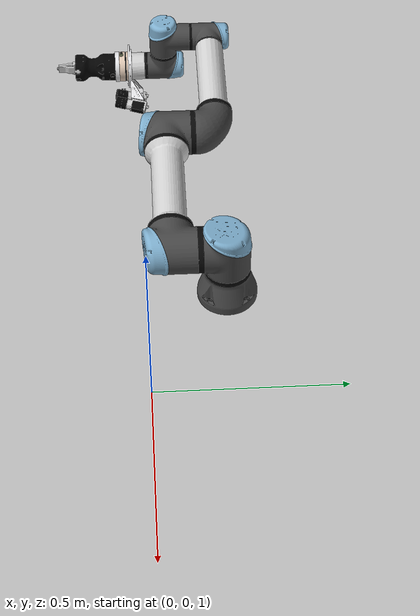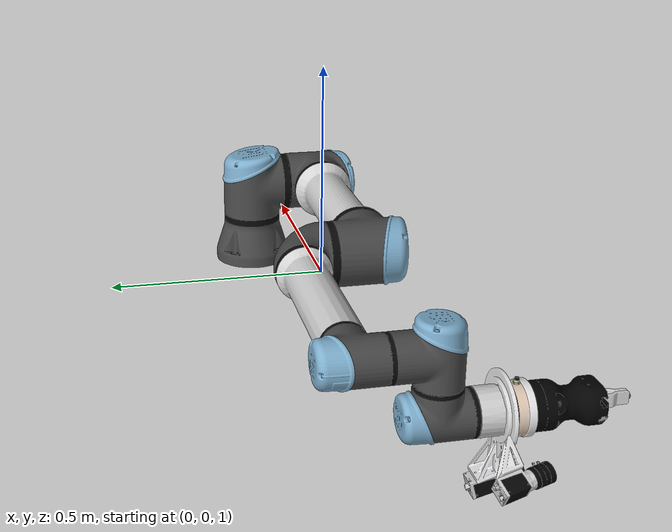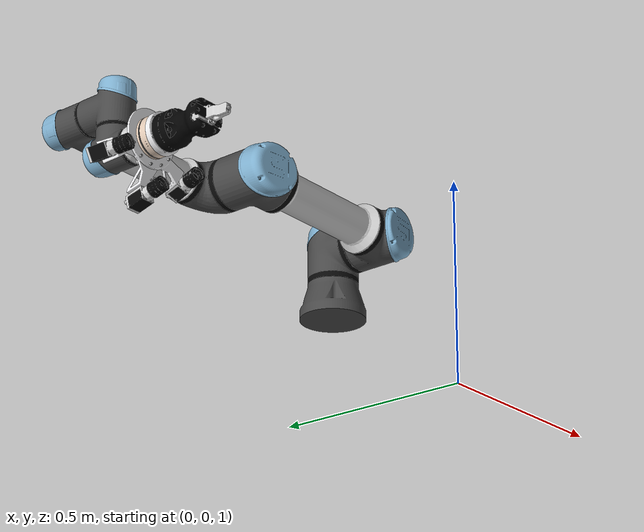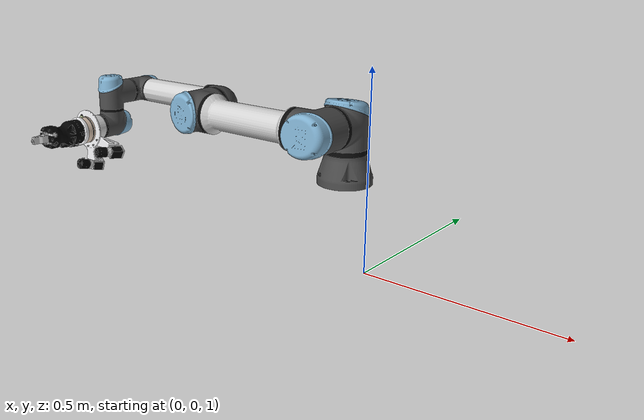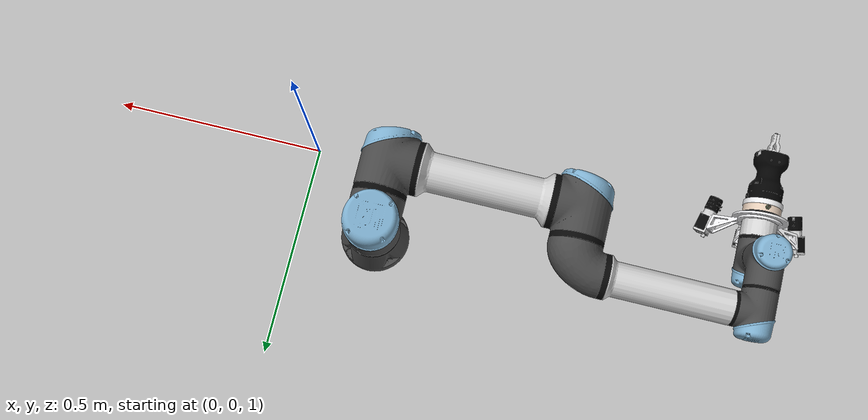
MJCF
<mujoco model="aic_world">
  <compiler angle="radian"/>

  <option gravity="0 0 -9.8" magnetic="5.5645e-06 2.28758e-05 -4.23884e-05"/>

  <visual>
    <global offwidth="1152" offheight="1024"/>
    <headlight ambient="0 0 0" diffuse="0 0 0" specular="0 0 0"/>
    <map znear="0.0025"/>
  </visual>

  <default>
    <default class="robot_unused"/>
  </default>

  <asset>
    <material name="material_bb4c831b689643226e5971fe331ef95e0c5c39f5d4107816252ab0347ed3238a_base_eSeries_UR5e_013-mesh" class="robot_unused" shininess="30" rgba="0.278431 0.278431 0.278431 1"/>
    <material name="material_bb4c831b689643226e5971fe331ef95e0c5c39f5d4107816252ab0347ed3238a_base_eSeries_UR5e_066-mesh" class="robot_unused" shininess="30" rgba="0.0313726 0.0313726 0.0313726 1"/>
    <material name="material_bb4c831b689643226e5971fe331ef95e0c5c39f5d4107816252ab0347ed3238a_shoulder_eSeries_UR5e_001-mesh" class="robot_unused" shininess="30" rgba="0.278431 0.278431 0.278431 1"/>
    <material name="material_bb4c831b689643226e5971fe331ef95e0c5c39f5d4107816252ab0347ed3238a_shoulder_eSeries_UR5e_067-mesh" class="robot_unused" shininess="30" rgba="0.0313726 0.0313726 0.0313726 1"/>
    <material name="material_bb4c831b689643226e5971fe331ef95e0c5c39f5d4107816252ab0347ed3238a_shoulder_eSeries_UR5e_068-mesh" class="robot_unused" shininess="30" rgba="0.490196 0.678431 0.8 1"/>
    <material name="material_bb4c831b689643226e5971fe331ef95e0c5c39f5d4107816252ab0347ed3238a_upperarm_merged_0" class="robot_unused" shininess="30" rgba="0.490196 0.678431 0.8 1"/>
    <material name="material_bb4c831b689643226e5971fe331ef95e0c5c39f5d4107816252ab0347ed3238a_upperarm_merged_1" class="robot_unused" shininess="30" rgba="0.278431 0.278431 0.278431 1"/>
    <material name="material_bb4c831b689643226e5971fe331ef95e0c5c39f5d4107816252ab0347ed3238a_upperarm_merged_2" class="robot_unused" shininess="30" rgba="0.0313726 0.0313726 0.0313726 1"/>
    <material name="material_bb4c831b689643226e5971fe331ef95e0c5c39f5d4107816252ab0347ed3238a_upperarm_eSeries_UR5e_073-mesh" class="robot_unused" shininess="30" rgba="0.819608 0.819608 0.819608 1"/>
    <material name="material_bb4c831b689643226e5971fe331ef95e0c5c39f5d4107816252ab0347ed3238a_forearm_merged_0" class="robot_unused" shininess="30" rgba="0.278431 0.278431 0.278431 1"/>
    <material name="material_bb4c831b689643226e5971fe331ef95e0c5c39f5d4107816252ab0347ed3238a_forearm_merged_1" class="robot_unused" shininess="30" rgba="0.0313726 0.0313726 0.0313726 1"/>
    <material name="material_bb4c831b689643226e5971fe331ef95e0c5c39f5d4107816252ab0347ed3238a_forearm_eSeries_UR5e_079-mesh" class="robot_unused" shininess="30" rgba="0.819608 0.819608 0.819608 1"/>
    <material name="material_bb4c831b689643226e5971fe331ef95e0c5c39f5d4107816252ab0347ed3238a_forearm_eSeries_UR5e_081-mesh" class="robot_unused" shininess="30" rgba="0.490196 0.678431 0.8 1"/>
    <material name="material_bb4c831b689643226e5971fe331ef95e0c5c39f5d4107816252ab0347ed3238a_wrist1_eSeries_UR5e_043-mesh" class="robot_unused" shininess="30" rgba="0.278431 0.278431 0.278431 1"/>
    <material name="material_bb4c831b689643226e5971fe331ef95e0c5c39f5d4107816252ab0347ed3238a_wrist1_eSeries_UR5e_083-mesh" class="robot_unused" shininess="30" rgba="0.490196 0.678431 0.8 1"/>
    <material name="material_bb4c831b689643226e5971fe331ef95e0c5c39f5d4107816252ab0347ed3238a_wrist1_eSeries_UR5e_084-mesh" class="robot_unused" shininess="30" rgba="0.0313726 0.0313726 0.0313726 1"/>
    <material name="material_bb4c831b689643226e5971fe331ef95e0c5c39f5d4107816252ab0347ed3238a_wrist2_eSeries_UR5e_049-mesh" class="robot_unused" shininess="30" rgba="0.278431 0.278431 0.278431 1"/>
    <material name="material_bb4c831b689643226e5971fe331ef95e0c5c39f5d4107816252ab0347ed3238a_wrist2_eSeries_UR5e_085-mesh" class="robot_unused" shininess="30" rgba="0.490196 0.678431 0.8 1"/>
    <material name="material_bb4c831b689643226e5971fe331ef95e0c5c39f5d4107816252ab0347ed3238a_wrist2_eSeries_UR5e_086-mesh" class="robot_unused" shininess="30" rgba="0.0313726 0.0313726 0.0313726 1"/>
    <material name="material_bb4c831b689643226e5971fe331ef95e0c5c39f5d4107816252ab0347ed3238a_wrist3_eSeries_UR5e_058-mesh" class="robot_unused" shininess="30" rgba="0.819608 0.819608 0.819608 1"/>
    <material name="material_77aecf6ee65958a58bba798a7e61b19213a681a9d1cfb48e37fb64f94dbd1ed2_cam_mount_visual_Cam_Mount.001" class="robot_unused" shininess="30" rgba="0.913725 0.913725 0.921569 1"/>
    <material name="material_77aecf6ee65958a58bba798a7e61b19213a681a9d1cfb48e37fb64f94dbd1ed2_cam_mount_visual_Cam_Mount.001_1" class="robot_unused" shininess="30" rgba="0.8 0.8 0.8 1"/>
    <material name="material_da0a7de639716d36573260e6b2cbbf5e041c6c33572c3d56607c19a7f3b4e1f0_basler_cam_visual_59871rev000.001" class="robot_unused" shininess="30" rgba="0.00784314 0.00784314 0.00784314 1"/>
    <material name="material_da0a7de639716d36573260e6b2cbbf5e041c6c33572c3d56607c19a7f3b4e1f0_basler_cam_visual_59871rev000.001_1" class="robot_unused" shininess="30" rgba="0.8 0.8 0.8 1"/>
    <material name="material_da0a7de639716d36573260e6b2cbbf5e041c6c33572c3d56607c19a7f3b4e1f0_basler_cam_visual_59871rev000.001_2" class="robot_unused" shininess="30" rgba="0.0196078 0.0196078 0.0196078 1"/>
    <material name="material_da0a7de639716d36573260e6b2cbbf5e041c6c33572c3d56607c19a7f3b4e1f0_basler_cam_visual_59871rev000.001_3" class="robot_unused" shininess="30" rgba="0.00392157 0.00392157 0.00392157 1"/>
    <material name="material_da0a7de639716d36573260e6b2cbbf5e041c6c33572c3d56607c19a7f3b4e1f0_basler_cam_visual_59871rev000.001_4" class="robot_unused" shininess="30" rgba="0.52549 0.52549 0.52549 1"/>
    <material name="material_ef10da9ad106c4dff912c5b813eab6adf887a181130890f0626184dba01c2bb2_axia_ft_sensor_visual_Axia80_M20.001" class="robot_unused" shininess="30" rgba="0.882353 0.792157 0.713726 1"/>
    <material name="material_ef10da9ad106c4dff912c5b813eab6adf887a181130890f0626184dba01c2bb2_axia_ft_sensor_visual_Axia80_M20.001_1" class="robot_unused" shininess="30" rgba="0.0196078 0.0196078 0.0196078 1"/>
    <material name="material_ef10da9ad106c4dff912c5b813eab6adf887a181130890f0626184dba01c2bb2_axia_ft_sensor_visual_Axia80_M20.001_2" class="robot_unused" shininess="30" rgba="0.8 0.564706 0.188235 1"/>
    <material name="material_ef10da9ad106c4dff912c5b813eab6adf887a181130890f0626184dba01c2bb2_axia_ft_sensor_visual_Axia80_M20.001_3" class="robot_unused" shininess="30" rgba="0.768627 0.811765 0.627451 1"/>
    <material name="material_ef10da9ad106c4dff912c5b813eab6adf887a181130890f0626184dba01c2bb2_axia_ft_sensor_visual_Axia80_M20.001_4" class="robot_unused" shininess="30" rgba="0.0117647 0.0117647 0.0117647 1"/>
    <material name="material_a356bb6a272d632104f139fc2b48a19577bee572dba59724b998cb71069c20f8_hande_base_visual_Cylinder.004" class="robot_unused" shininess="30" rgba="0.913725 0.913725 0.921569 1"/>
    <material name="material_a356bb6a272d632104f139fc2b48a19577bee572dba59724b998cb71069c20f8_hande_base_visual_Cylinder.004_1" class="robot_unused" shininess="30" rgba="0.00392157 0.00392157 0.00392157 1"/>
    <material name="material_a356bb6a272d632104f139fc2b48a19577bee572dba59724b998cb71069c20f8_hande_base_visual_Cylinder.004_2" class="robot_unused" shininess="30" rgba="0.784314 0.823529 0.847059 1"/>
    <material name="material_a356bb6a272d632104f139fc2b48a19577bee572dba59724b998cb71069c20f8_hande_base_visual_Cylinder.004_3" class="robot_unused" shininess="30" rgba="0.0117647 0.0117647 0.0117647 1"/>
    <material name="material_a356bb6a272d632104f139fc2b48a19577bee572dba59724b998cb71069c20f8_hande_base_visual_Cylinder.004_4" class="robot_unused" shininess="30" rgba="0.00784314 0.00784314 0.00784314 1"/>
    <material name="material_a356bb6a272d632104f139fc2b48a19577bee572dba59724b998cb71069c20f8_hande_base_visual_Cylinder.004_5" class="robot_unused" shininess="30" rgba="0.203922 0.203922 0.203922 1"/>
    <material name="material_a356bb6a272d632104f139fc2b48a19577bee572dba59724b998cb71069c20f8_hande_base_visual_Cylinder.004_6" class="robot_unused" shininess="30" rgba="0.5 0.5 0.5 1"/>
    <material name="material_a356bb6a272d632104f139fc2b48a19577bee572dba59724b998cb71069c20f8_hande_finger_visual_Finger.001" class="robot_unused" shininess="30" rgba="0.8 0.8 0.8 1"/>
    <mesh name="a0ab51268db2dd6ba30e2e14e1f8befeabfff6f0fbdfd420b564678df289a3c0_base.stl" class="robot_unused" content_type="model/stl" file="base-d994a04ff52ddcdf6d91bb6d4fcfff9b1425c18e.stl"/>
    <mesh name="bb4c831b689643226e5971fe331ef95e0c5c39f5d4107816252ab0347ed3238a_base_eSeries_UR5e_013-mesh" class="robot_unused" content_type="model/obj" file="bb4c831b689643226e5971fe331ef95e0c5c39f5d4107816252ab0347ed3238a_base_eSeries_UR5e_013-mesh-ae81e78d79cde8959e1b4051bcd48b43dd65d15f.obj" inertia="shell"/>
    <mesh name="bb4c831b689643226e5971fe331ef95e0c5c39f5d4107816252ab0347ed3238a_base_eSeries_UR5e_066-mesh" class="robot_unused" content_type="model/obj" file="bb4c831b689643226e5971fe331ef95e0c5c39f5d4107816252ab0347ed3238a_base_eSeries_UR5e_066-mesh-dd543f6667f50bd4643e49be303d92a0352f3d30.obj" inertia="shell"/>
    <mesh name="a0ab51268db2dd6ba30e2e14e1f8befeabfff6f0fbdfd420b564678df289a3c0_shoulder.stl" class="robot_unused" content_type="model/stl" file="shoulder-a83506202923a888b5b5d3c371edb9e13f236336.stl"/>
    <mesh name="bb4c831b689643226e5971fe331ef95e0c5c39f5d4107816252ab0347ed3238a_shoulder_eSeries_UR5e_001-mesh" class="robot_unused" content_type="model/obj" file="bb4c831b689643226e5971fe331ef95e0c5c39f5d4107816252ab0347ed3238a_shoulder_eSeries_UR5e_001-mesh-272c600201fcdab3fc8f4dad6fa4cd25579d6c3e.obj" inertia="shell"/>
    <mesh name="bb4c831b689643226e5971fe331ef95e0c5c39f5d4107816252ab0347ed3238a_shoulder_eSeries_UR5e_067-mesh" class="robot_unused" content_type="model/obj" file="bb4c831b689643226e5971fe331ef95e0c5c39f5d4107816252ab0347ed3238a_shoulder_eSeries_UR5e_067-mesh-ff08040e3ff3e66b2fcbba78dad276e67a66f2a9.obj" inertia="shell"/>
    <mesh name="bb4c831b689643226e5971fe331ef95e0c5c39f5d4107816252ab0347ed3238a_shoulder_eSeries_UR5e_068-mesh" class="robot_unused" content_type="model/obj" file="bb4c831b689643226e5971fe331ef95e0c5c39f5d4107816252ab0347ed3238a_shoulder_eSeries_UR5e_068-mesh-e6646b5927376d07178c45377b122d83ca5d8079.obj" inertia="shell"/>
    <mesh name="a0ab51268db2dd6ba30e2e14e1f8befeabfff6f0fbdfd420b564678df289a3c0_upperarm.stl" class="robot_unused" content_type="model/stl" file="upperarm-03c2bdced333d049d7ff8fbd721d7d8230d808bc.stl"/>
    <mesh name="bb4c831b689643226e5971fe331ef95e0c5c39f5d4107816252ab0347ed3238a_upperarm_merged_0" class="robot_unused" content_type="model/obj" file="bb4c831b689643226e5971fe331ef95e0c5c39f5d4107816252ab0347ed3238a_upperarm_merged_0-88fa3cf6b01946f867aa3ae8c3267e98b30b8869.obj" inertia="shell"/>
    <mesh name="bb4c831b689643226e5971fe331ef95e0c5c39f5d4107816252ab0347ed3238a_upperarm_merged_1" class="robot_unused" content_type="model/obj" file="bb4c831b689643226e5971fe331ef95e0c5c39f5d4107816252ab0347ed3238a_upperarm_merged_1-6caf0ab73dc274153cbd7f6f7ed6bb8d05f86b64.obj" inertia="shell"/>
    <mesh name="bb4c831b689643226e5971fe331ef95e0c5c39f5d4107816252ab0347ed3238a_upperarm_merged_2" class="robot_unused" content_type="model/obj" file="bb4c831b689643226e5971fe331ef95e0c5c39f5d4107816252ab0347ed3238a_upperarm_merged_2-ffa0d83ca1ca182a7f88f6b6370c57fb8458e1a1.obj" inertia="shell"/>
    <mesh name="bb4c831b689643226e5971fe331ef95e0c5c39f5d4107816252ab0347ed3238a_upperarm_eSeries_UR5e_073-mesh" class="robot_unused" content_type="model/obj" file="bb4c831b689643226e5971fe331ef95e0c5c39f5d4107816252ab0347ed3238a_upperarm_eSeries_UR5e_073-mesh-80ecc8c6aa2daa7af816d47c8b6c7336f8c8ab2e.obj" inertia="shell"/>
    <mesh name="a0ab51268db2dd6ba30e2e14e1f8befeabfff6f0fbdfd420b564678df289a3c0_forearm.stl" class="robot_unused" content_type="model/stl" file="forearm-95860729b3e4915567db264330b9ab276f0c8308.stl"/>
    <mesh name="bb4c831b689643226e5971fe331ef95e0c5c39f5d4107816252ab0347ed3238a_forearm_merged_0" class="robot_unused" content_type="model/obj" file="bb4c831b689643226e5971fe331ef95e0c5c39f5d4107816252ab0347ed3238a_forearm_merged_0-b1119653aa5b99527a8ffdc95deddded03606e49.obj" inertia="shell"/>
    <mesh name="bb4c831b689643226e5971fe331ef95e0c5c39f5d4107816252ab0347ed3238a_forearm_merged_1" class="robot_unused" content_type="model/obj" file="bb4c831b689643226e5971fe331ef95e0c5c39f5d4107816252ab0347ed3238a_forearm_merged_1-90d771496e3e60c8c49b0f907214218e12010f56.obj" inertia="shell"/>
    <mesh name="bb4c831b689643226e5971fe331ef95e0c5c39f5d4107816252ab0347ed3238a_forearm_eSeries_UR5e_079-mesh" class="robot_unused" content_type="model/obj" file="bb4c831b689643226e5971fe331ef95e0c5c39f5d4107816252ab0347ed3238a_forearm_eSeries_UR5e_079-mesh-3af239601fa1722841f61cefe776f3ac82925295.obj" inertia="shell"/>
    <mesh name="bb4c831b689643226e5971fe331ef95e0c5c39f5d4107816252ab0347ed3238a_forearm_eSeries_UR5e_081-mesh" class="robot_unused" content_type="model/obj" file="bb4c831b689643226e5971fe331ef95e0c5c39f5d4107816252ab0347ed3238a_forearm_eSeries_UR5e_081-mesh-295cc91f1da8d729521b96ae635c9f65e0f9235d.obj" inertia="shell"/>
    <mesh name="a0ab51268db2dd6ba30e2e14e1f8befeabfff6f0fbdfd420b564678df289a3c0_wrist1.stl" class="robot_unused" content_type="model/stl" file="wrist1-d0aff1dbf858639fbad7a22318ecfa5fba436f30.stl"/>
    <mesh name="bb4c831b689643226e5971fe331ef95e0c5c39f5d4107816252ab0347ed3238a_wrist1_eSeries_UR5e_043-mesh" class="robot_unused" content_type="model/obj" file="bb4c831b689643226e5971fe331ef95e0c5c39f5d4107816252ab0347ed3238a_wrist1_eSeries_UR5e_043-mesh-62b7c0392b368ddedc2465d9c00c00e610d20f5a.obj" inertia="shell"/>
    <mesh name="bb4c831b689643226e5971fe331ef95e0c5c39f5d4107816252ab0347ed3238a_wrist1_eSeries_UR5e_083-mesh" class="robot_unused" content_type="model/obj" file="bb4c831b689643226e5971fe331ef95e0c5c39f5d4107816252ab0347ed3238a_wrist1_eSeries_UR5e_083-mesh-cabbadefb6102d1556a4ee64c8bd36cad8056884.obj" inertia="shell"/>
    <mesh name="bb4c831b689643226e5971fe331ef95e0c5c39f5d4107816252ab0347ed3238a_wrist1_eSeries_UR5e_084-mesh" class="robot_unused" content_type="model/obj" file="bb4c831b689643226e5971fe331ef95e0c5c39f5d4107816252ab0347ed3238a_wrist1_eSeries_UR5e_084-mesh-ac1b41f582ea0ee06c11c0892f88e3251a6546be.obj" inertia="shell"/>
    <mesh name="a0ab51268db2dd6ba30e2e14e1f8befeabfff6f0fbdfd420b564678df289a3c0_wrist2.stl" class="robot_unused" content_type="model/stl" file="wrist2-777eba24b0996c38308995e2e7740d22a77ee8a8.stl"/>
    <mesh name="bb4c831b689643226e5971fe331ef95e0c5c39f5d4107816252ab0347ed3238a_wrist2_eSeries_UR5e_049-mesh" class="robot_unused" content_type="model/obj" file="bb4c831b689643226e5971fe331ef95e0c5c39f5d4107816252ab0347ed3238a_wrist2_eSeries_UR5e_049-mesh-1e943fb734424cb597a1a044d2099d5fdfbb4313.obj" inertia="shell"/>
    <mesh name="bb4c831b689643226e5971fe331ef95e0c5c39f5d4107816252ab0347ed3238a_wrist2_eSeries_UR5e_085-mesh" class="robot_unused" content_type="model/obj" file="bb4c831b689643226e5971fe331ef95e0c5c39f5d4107816252ab0347ed3238a_wrist2_eSeries_UR5e_085-mesh-60da050b95a6d5e25db5fe59ffab86db07961b4c.obj" inertia="shell"/>
    <mesh name="bb4c831b689643226e5971fe331ef95e0c5c39f5d4107816252ab0347ed3238a_wrist2_eSeries_UR5e_086-mesh" class="robot_unused" content_type="model/obj" file="bb4c831b689643226e5971fe331ef95e0c5c39f5d4107816252ab0347ed3238a_wrist2_eSeries_UR5e_086-mesh-a15e99ce0f74c0a8f995e5172279d0dfcac6845e.obj" inertia="shell"/>
    <mesh name="a0ab51268db2dd6ba30e2e14e1f8befeabfff6f0fbdfd420b564678df289a3c0_wrist3.stl" class="robot_unused" content_type="model/stl" file="wrist3-f7f56f92b9aad1eab55349b28bbe751f72de21da.stl"/>
    <mesh name="bb4c831b689643226e5971fe331ef95e0c5c39f5d4107816252ab0347ed3238a_wrist3_eSeries_UR5e_058-mesh" class="robot_unused" content_type="model/obj" file="bb4c831b689643226e5971fe331ef95e0c5c39f5d4107816252ab0347ed3238a_wrist3_eSeries_UR5e_058-mesh-67fef77ed5577e1d953e2e77da568e9a7d2cb750.obj" inertia="shell"/>
    <mesh name="77aecf6ee65958a58bba798a7e61b19213a681a9d1cfb48e37fb64f94dbd1ed2_cam_mount_visual_Cam_Mount.001" class="robot_unused" content_type="model/obj" file="77aecf6ee65958a58bba798a7e61b19213a681a9d1cfb48e37fb64f94dbd1ed2_cam_mount_visual_Cam_Mount.001-723ff43f362d0710a4bac575e9d2b9597ae995d6.obj" inertia="shell"/>
    <mesh name="77aecf6ee65958a58bba798a7e61b19213a681a9d1cfb48e37fb64f94dbd1ed2_cam_mount_visual_Cam_Mount.001_1" class="robot_unused" content_type="model/obj" file="77aecf6ee65958a58bba798a7e61b19213a681a9d1cfb48e37fb64f94dbd1ed2_cam_mount_visual_Cam_Mount.001_1-0c31e96946f6e4a992e40f16ffd143303f2fc693.obj" inertia="shell"/>
    <mesh name="da0a7de639716d36573260e6b2cbbf5e041c6c33572c3d56607c19a7f3b4e1f0_basler_cam_visual_59871rev000.001" class="robot_unused" content_type="model/obj" file="da0a7de639716d36573260e6b2cbbf5e041c6c33572c3d56607c19a7f3b4e1f0_basler_cam_visual_59871rev000.001-ea790e2c931ae136790eb9db5c9297b0a632fd93.obj" inertia="shell"/>
    <mesh name="da0a7de639716d36573260e6b2cbbf5e041c6c33572c3d56607c19a7f3b4e1f0_basler_cam_visual_59871rev000.001_1" class="robot_unused" content_type="model/obj" file="da0a7de639716d36573260e6b2cbbf5e041c6c33572c3d56607c19a7f3b4e1f0_basler_cam_visual_59871rev000.001_1-28ccf15525b0de2a7b9afa152d290efc33be18a4.obj" inertia="shell"/>
    <mesh name="da0a7de639716d36573260e6b2cbbf5e041c6c33572c3d56607c19a7f3b4e1f0_basler_cam_visual_59871rev000.001_2" class="robot_unused" content_type="model/obj" file="da0a7de639716d36573260e6b2cbbf5e041c6c33572c3d56607c19a7f3b4e1f0_basler_cam_visual_59871rev000.001_2-36c96f981e71c1cf6b31da79577e86d871a3ec2d.obj" inertia="shell"/>
    <mesh name="da0a7de639716d36573260e6b2cbbf5e041c6c33572c3d56607c19a7f3b4e1f0_basler_cam_visual_59871rev000.001_3" class="robot_unused" content_type="model/obj" file="da0a7de639716d36573260e6b2cbbf5e041c6c33572c3d56607c19a7f3b4e1f0_basler_cam_visual_59871rev000.001_3-11d42f5e41dcfed76206985524331834024f1c81.obj" inertia="shell"/>
    <mesh name="da0a7de639716d36573260e6b2cbbf5e041c6c33572c3d56607c19a7f3b4e1f0_basler_cam_visual_59871rev000.001_4" class="robot_unused" content_type="model/obj" file="da0a7de639716d36573260e6b2cbbf5e041c6c33572c3d56607c19a7f3b4e1f0_basler_cam_visual_59871rev000.001_4-5588717adcbdf83f1ff65b65be3ac368dbe69164.obj" inertia="shell"/>
    <mesh name="ef10da9ad106c4dff912c5b813eab6adf887a181130890f0626184dba01c2bb2_axia_ft_sensor_visual_Axia80_M20.001" class="robot_unused" content_type="model/obj" file="ef10da9ad106c4dff912c5b813eab6adf887a181130890f0626184dba01c2bb2_axia_ft_sensor_visual_Axia80_M20.001-e71568379caa7fc7691a233f5ef4487cf57b0b6a.obj" inertia="shell"/>
    <mesh name="ef10da9ad106c4dff912c5b813eab6adf887a181130890f0626184dba01c2bb2_axia_ft_sensor_visual_Axia80_M20.001_1" class="robot_unused" content_type="model/obj" file="ef10da9ad106c4dff912c5b813eab6adf887a181130890f0626184dba01c2bb2_axia_ft_sensor_visual_Axia80_M20.001_1-47b7cd0ada962512b0e7fc9aacb9d4a493a53870.obj" inertia="shell"/>
    <mesh name="ef10da9ad106c4dff912c5b813eab6adf887a181130890f0626184dba01c2bb2_axia_ft_sensor_visual_Axia80_M20.001_2" class="robot_unused" content_type="model/obj" file="ef10da9ad106c4dff912c5b813eab6adf887a181130890f0626184dba01c2bb2_axia_ft_sensor_visual_Axia80_M20.001_2-c87bfd828a552023b637d27572f31e95f0b18899.obj" inertia="shell"/>
    <mesh name="ef10da9ad106c4dff912c5b813eab6adf887a181130890f0626184dba01c2bb2_axia_ft_sensor_visual_Axia80_M20.001_3" class="robot_unused" content_type="model/obj" file="ef10da9ad106c4dff912c5b813eab6adf887a181130890f0626184dba01c2bb2_axia_ft_sensor_visual_Axia80_M20.001_3-0fc8cff22b030a6251e69b2c2f367230b19033b0.obj" inertia="shell"/>
    <mesh name="ef10da9ad106c4dff912c5b813eab6adf887a181130890f0626184dba01c2bb2_axia_ft_sensor_visual_Axia80_M20.001_4" class="robot_unused" content_type="model/obj" file="ef10da9ad106c4dff912c5b813eab6adf887a181130890f0626184dba01c2bb2_axia_ft_sensor_visual_Axia80_M20.001_4-1a923e185a96ad2b7c7e534e69d06147b1600c47.obj" inertia="shell"/>
    <mesh name="a356bb6a272d632104f139fc2b48a19577bee572dba59724b998cb71069c20f8_hande_base_visual_Cylinder.004" class="robot_unused" content_type="model/obj" file="a356bb6a272d632104f139fc2b48a19577bee572dba59724b998cb71069c20f8_hande_base_visual_Cylinder.004-ccd4fe0ca5775408071ac4229bd0b389a1de7615.obj" inertia="shell"/>
    <mesh name="a356bb6a272d632104f139fc2b48a19577bee572dba59724b998cb71069c20f8_hande_base_visual_Cylinder.004_1" class="robot_unused" content_type="model/obj" file="a356bb6a272d632104f139fc2b48a19577bee572dba59724b998cb71069c20f8_hande_base_visual_Cylinder.004_1-3bf56dcca5fbeb798080096f8d0bd5dcaa66c950.obj" inertia="shell"/>
    <mesh name="a356bb6a272d632104f139fc2b48a19577bee572dba59724b998cb71069c20f8_hande_base_visual_Cylinder.004_2" class="robot_unused" content_type="model/obj" file="a356bb6a272d632104f139fc2b48a19577bee572dba59724b998cb71069c20f8_hande_base_visual_Cylinder.004_2-0a53d4ce4f2094e48035a814ff02b25c18748ea6.obj" inertia="shell"/>
    <mesh name="a356bb6a272d632104f139fc2b48a19577bee572dba59724b998cb71069c20f8_hande_base_visual_Cylinder.004_3" class="robot_unused" content_type="model/obj" file="a356bb6a272d632104f139fc2b48a19577bee572dba59724b998cb71069c20f8_hande_base_visual_Cylinder.004_3-cca323fd4ea1d742b710ee683d2c1130fcc515bb.obj" inertia="shell"/>
    <mesh name="a356bb6a272d632104f139fc2b48a19577bee572dba59724b998cb71069c20f8_hande_base_visual_Cylinder.004_4" class="robot_unused" content_type="model/obj" file="a356bb6a272d632104f139fc2b48a19577bee572dba59724b998cb71069c20f8_hande_base_visual_Cylinder.004_4-4164421b7c7d1873f13321fa07c607a5bfa6422d.obj" inertia="shell"/>
    <mesh name="a356bb6a272d632104f139fc2b48a19577bee572dba59724b998cb71069c20f8_hande_base_visual_Cylinder.004_5" class="robot_unused" content_type="model/obj" file="a356bb6a272d632104f139fc2b48a19577bee572dba59724b998cb71069c20f8_hande_base_visual_Cylinder.004_5-227d9a518ecd4b9f11b8e0f29fd25d20d4e7de87.obj" inertia="shell"/>
    <mesh name="a356bb6a272d632104f139fc2b48a19577bee572dba59724b998cb71069c20f8_hande_base_visual_Cylinder.004_6" class="robot_unused" content_type="model/obj" file="a356bb6a272d632104f139fc2b48a19577bee572dba59724b998cb71069c20f8_hande_base_visual_Cylinder.004_6-2b45d6510840057a8742e3e457a4715ce6816a3c.obj" inertia="shell"/>
    <mesh name="a356bb6a272d632104f139fc2b48a19577bee572dba59724b998cb71069c20f8_hande_finger_visual_Finger.001" class="robot_unused" content_type="model/obj" file="a356bb6a272d632104f139fc2b48a19577bee572dba59724b998cb71069c20f8_hande_finger_visual_Finger.001-dfdab7afd4748b2dd71ea2c1c7fbe159b76dfbe5.obj" inertia="shell"/>
  </asset>

  <worldbody>
    <body name="tabletop" pos="-0.2 0.2 1.14" quat="1 0 0 0">
      <inertial pos="0 0 0" quat="0.5 0.5 -0.5 0.5" mass="4" diaginertia="0.0072 0.00443333 0.00443333"/>
      <geom name="tabletop_fixed_joint_lump__base_link_inertia_collision" class="robot_unused" type="mesh" group="3" mesh="a0ab51268db2dd6ba30e2e14e1f8befeabfff6f0fbdfd420b564678df289a3c0_base.stl"/>
      <geom name="tabletop_fixed_joint_lump__base_link_inertia_visual" class="robot_unused" type="mesh" contype="0" conaffinity="0" material="material_bb4c831b689643226e5971fe331ef95e0c5c39f5d4107816252ab0347ed3238a_base_eSeries_UR5e_013-mesh" mesh="bb4c831b689643226e5971fe331ef95e0c5c39f5d4107816252ab0347ed3238a_base_eSeries_UR5e_013-mesh"/>
      <geom name="tabletop_fixed_joint_lump__base_link_inertia_visual_0" class="robot_unused" type="mesh" contype="0" conaffinity="0" material="material_bb4c831b689643226e5971fe331ef95e0c5c39f5d4107816252ab0347ed3238a_base_eSeries_UR5e_066-mesh" mesh="bb4c831b689643226e5971fe331ef95e0c5c39f5d4107816252ab0347ed3238a_base_eSeries_UR5e_066-mesh"/>
      <body name="shoulder_link" pos="-5.80488e-10 2.03378e-09 0.1625">
        <inertial pos="0 -0.00193 -0.02561" quat="0.73527 -0.287588 0.218944 0.573354" mass="3.761" diaginertia="0.00703079 0.0070003 0.00602478"/>
        <joint name="shoulder_pan_joint" class="robot_unused" pos="0 0 0" axis="0 0 1" limited="true" range="-6.28319 6.28319" damping="1.0" armature="0.1"/>
        <geom name="shoulder_link_collision" class="robot_unused" quat="0 0 0 1" type="mesh" group="3" mesh="a0ab51268db2dd6ba30e2e14e1f8befeabfff6f0fbdfd420b564678df289a3c0_shoulder.stl"/>
        <geom name="shoulder_link_visual" class="robot_unused" quat="0 0 0 1" type="mesh" contype="0" conaffinity="0" material="material_bb4c831b689643226e5971fe331ef95e0c5c39f5d4107816252ab0347ed3238a_shoulder_eSeries_UR5e_001-mesh" mesh="bb4c831b689643226e5971fe331ef95e0c5c39f5d4107816252ab0347ed3238a_shoulder_eSeries_UR5e_001-mesh"/>
        <geom name="shoulder_link_visual_0" class="robot_unused" pos="0 0 0" quat="0 0 0 1" type="mesh" contype="0" conaffinity="0" material="material_bb4c831b689643226e5971fe331ef95e0c5c39f5d4107816252ab0347ed3238a_shoulder_eSeries_UR5e_067-mesh" mesh="bb4c831b689643226e5971fe331ef95e0c5c39f5d4107816252ab0347ed3238a_shoulder_eSeries_UR5e_067-mesh"/>
        <geom name="shoulder_link_visual_1" class="robot_unused" pos="0 0 0" quat="0 0 0 1" type="mesh" contype="0" conaffinity="0" material="material_bb4c831b689643226e5971fe331ef95e0c5c39f5d4107816252ab0347ed3238a_shoulder_eSeries_UR5e_068-mesh" mesh="bb4c831b689643226e5971fe331ef95e0c5c39f5d4107816252ab0347ed3238a_shoulder_eSeries_UR5e_068-mesh"/>
        <body name="upper_arm_link" pos="3.45826e-09 -5.75052e-08 -9.9e-09" quat="0.70710678 0.70710678 0 0">
          <inertial pos="-0.2125 0 0.11336" quat="0.500275 0.499641 0.500368 0.499716" mass="8.058" diaginertia="0.333881 0.332472 0.0150588"/>
          <joint name="shoulder_lift_joint" class="robot_unused" pos="0 0 0" axis="0 0 1" limited="true" range="-6.28319 6.28319" damping="1.0" armature="0.1"/>
          <geom name="upper_arm_link_collision" class="robot_unused" pos="0 0 0.138" quat="0.5 0.5 -0.5 -0.5" type="mesh" group="3" mesh="a0ab51268db2dd6ba30e2e14e1f8befeabfff6f0fbdfd420b564678df289a3c0_upperarm.stl"/>
          <geom name="upper_arm_link_visual" class="robot_unused" pos="0 0 0.138" quat="0.5 0.5 -0.5 -0.5" type="mesh" contype="0" conaffinity="0" material="material_bb4c831b689643226e5971fe331ef95e0c5c39f5d4107816252ab0347ed3238a_upperarm_merged_0" mesh="bb4c831b689643226e5971fe331ef95e0c5c39f5d4107816252ab0347ed3238a_upperarm_merged_0"/>
          <geom name="upper_arm_link_visual_0" class="robot_unused" pos="0 0 0.138" quat="0.5 0.5 -0.5 -0.5" type="mesh" contype="0" conaffinity="0" material="material_bb4c831b689643226e5971fe331ef95e0c5c39f5d4107816252ab0347ed3238a_upperarm_merged_1" mesh="bb4c831b689643226e5971fe331ef95e0c5c39f5d4107816252ab0347ed3238a_upperarm_merged_1"/>
          <geom name="upper_arm_link_visual_1" class="robot_unused" pos="0 0 0.138" quat="0.5 0.5 -0.5 -0.5" type="mesh" contype="0" conaffinity="0" material="material_bb4c831b689643226e5971fe331ef95e0c5c39f5d4107816252ab0347ed3238a_upperarm_merged_2" mesh="bb4c831b689643226e5971fe331ef95e0c5c39f5d4107816252ab0347ed3238a_upperarm_merged_2"/>
          <geom name="upper_arm_link_visual_2" class="robot_unused" pos="0 0 0.138" quat="0.5 0.5 -0.5 -0.5" type="mesh" contype="0" conaffinity="0" material="material_bb4c831b689643226e5971fe331ef95e0c5c39f5d4107816252ab0347ed3238a_upperarm_eSeries_UR5e_073-mesh" mesh="bb4c831b689643226e5971fe331ef95e0c5c39f5d4107816252ab0347ed3238a_upperarm_eSeries_UR5e_073-mesh"/>
          <body name="forearm_link" pos="-0.425 -7.06123e-08 6.00811e-08">
            <inertial pos="-0.2422 0 0.0265" quat="0.501301 0.498381 0.510711 0.489375" mass="2.846" diaginertia="0.0787927 0.0785102 0.00397103"/>
            <joint name="elbow_joint" class="robot_unused" pos="0 0 0" axis="0 0 1" limited="true" range="-3.14159 3.14159" damping="1.0" armature="0.1"/>
            <geom name="forearm_link_collision" class="robot_unused" pos="0 0 0.007" quat="0.5 0.5 -0.5 -0.5" type="mesh" group="3" mesh="a0ab51268db2dd6ba30e2e14e1f8befeabfff6f0fbdfd420b564678df289a3c0_forearm.stl"/>
            <geom name="forearm_link_visual" class="robot_unused" pos="0 0 0.007" quat="0.5 0.5 -0.5 -0.5" type="mesh" contype="0" conaffinity="0" material="material_bb4c831b689643226e5971fe331ef95e0c5c39f5d4107816252ab0347ed3238a_forearm_merged_0" mesh="bb4c831b689643226e5971fe331ef95e0c5c39f5d4107816252ab0347ed3238a_forearm_merged_0"/>
            <geom name="forearm_link_visual_0" class="robot_unused" pos="0 0 0.007" quat="0.5 0.5 -0.5 -0.5" type="mesh" contype="0" conaffinity="0" material="material_bb4c831b689643226e5971fe331ef95e0c5c39f5d4107816252ab0347ed3238a_forearm_merged_1" mesh="bb4c831b689643226e5971fe331ef95e0c5c39f5d4107816252ab0347ed3238a_forearm_merged_1"/>
            <geom name="forearm_link_visual_1" class="robot_unused" pos="0 0 0.007" quat="0.5 0.5 -0.5 -0.5" type="mesh" contype="0" conaffinity="0" material="material_bb4c831b689643226e5971fe331ef95e0c5c39f5d4107816252ab0347ed3238a_forearm_eSeries_UR5e_079-mesh" mesh="bb4c831b689643226e5971fe331ef95e0c5c39f5d4107816252ab0347ed3238a_forearm_eSeries_UR5e_079-mesh"/>
            <geom name="forearm_link_visual_2" class="robot_unused" pos="0 0 0.007" quat="0.5 0.5 -0.5 -0.5" type="mesh" contype="0" conaffinity="0" material="material_bb4c831b689643226e5971fe331ef95e0c5c39f5d4107816252ab0347ed3238a_forearm_eSeries_UR5e_081-mesh" mesh="bb4c831b689643226e5971fe331ef95e0c5c39f5d4107816252ab0347ed3238a_forearm_eSeries_UR5e_081-mesh"/>
            <body name="wrist_1_link" pos="-0.3922 -1.5324e-07 0.1333">
              <inertial pos="0 -0.01634 -0.0018" quat="0.482884 0.875621 0.0101022 -0.00281842" mass="1.37" diaginertia="0.00165502 0.00142363 0.00119868"/>
              <joint name="wrist_1_joint" class="robot_unused" pos="0 0 0" axis="0 0 1" limited="true" range="-6.28319 6.28319" damping="1.0" armature="0.1"/>
              <geom name="wrist_1_link_collision" class="robot_unused" pos="0 0 -0.127" quat="0.707107 0.707107 0 0" type="mesh" group="3" mesh="a0ab51268db2dd6ba30e2e14e1f8befeabfff6f0fbdfd420b564678df289a3c0_wrist1.stl"/>
              <geom name="wrist_1_link_visual" class="robot_unused" pos="0 0 -0.127" quat="0.707107 0.707107 0 0" type="mesh" contype="0" conaffinity="0" material="material_bb4c831b689643226e5971fe331ef95e0c5c39f5d4107816252ab0347ed3238a_wrist1_eSeries_UR5e_043-mesh" mesh="bb4c831b689643226e5971fe331ef95e0c5c39f5d4107816252ab0347ed3238a_wrist1_eSeries_UR5e_043-mesh"/>
              <geom name="wrist_1_link_visual_0" class="robot_unused" pos="0 0 -0.127" quat="0.707107 0.707107 0 0" type="mesh" contype="0" conaffinity="0" material="material_bb4c831b689643226e5971fe331ef95e0c5c39f5d4107816252ab0347ed3238a_wrist1_eSeries_UR5e_083-mesh" mesh="bb4c831b689643226e5971fe331ef95e0c5c39f5d4107816252ab0347ed3238a_wrist1_eSeries_UR5e_083-mesh"/>
              <geom name="wrist_1_link_visual_1" class="robot_unused" pos="0 0 -0.127" quat="0.707107 0.707107 0 0" type="mesh" contype="0" conaffinity="0" material="material_bb4c831b689643226e5971fe331ef95e0c5c39f5d4107816252ab0347ed3238a_wrist1_eSeries_UR5e_084-mesh" mesh="bb4c831b689643226e5971fe331ef95e0c5c39f5d4107816252ab0347ed3238a_wrist1_eSeries_UR5e_084-mesh"/>
              <body name="wrist_2_link" pos="-6.99961e-08 -0.0996999 -4.9796e-08" quat="0.70710678 0.70710678 0 0">
                <inertial pos="0 0.01634 -0.0018" quat="0.759847 0.649632 -0.0119443 0.0216264" mass="1.3" diaginertia="0.00135637 0.00128607 0.00095814"/>
                <joint name="wrist_2_joint" class="robot_unused" pos="0 0 0" axis="0 0 1" limited="true" range="-6.28319 6.28319" damping="1.0" armature="0.1"/>
                <geom name="wrist_2_link_collision" class="robot_unused" pos="0 0 -0.0997" quat="1 0 0 0" type="mesh" group="3" mesh="a0ab51268db2dd6ba30e2e14e1f8befeabfff6f0fbdfd420b564678df289a3c0_wrist2.stl"/>
                <geom name="wrist_2_link_visual" class="robot_unused" pos="0 0 -0.0997" quat="1 0 0 0" type="mesh" contype="0" conaffinity="0" material="material_bb4c831b689643226e5971fe331ef95e0c5c39f5d4107816252ab0347ed3238a_wrist2_eSeries_UR5e_049-mesh" mesh="bb4c831b689643226e5971fe331ef95e0c5c39f5d4107816252ab0347ed3238a_wrist2_eSeries_UR5e_049-mesh"/>
                <geom name="wrist_2_link_visual_0" class="robot_unused" pos="0 0 -0.0997" quat="1 0 0 0" type="mesh" contype="0" conaffinity="0" material="material_bb4c831b689643226e5971fe331ef95e0c5c39f5d4107816252ab0347ed3238a_wrist2_eSeries_UR5e_085-mesh" mesh="bb4c831b689643226e5971fe331ef95e0c5c39f5d4107816252ab0347ed3238a_wrist2_eSeries_UR5e_085-mesh"/>
                <geom name="wrist_2_link_visual_1" class="robot_unused" pos="0 0 -0.0997" quat="1 0 0 0" type="mesh" contype="0" conaffinity="0" material="material_bb4c831b689643226e5971fe331ef95e0c5c39f5d4107816252ab0347ed3238a_wrist2_eSeries_UR5e_086-mesh" mesh="bb4c831b689643226e5971fe331ef95e0c5c39f5d4107816252ab0347ed3238a_wrist2_eSeries_UR5e_086-mesh"/>
                <body name="wrist_3_link" pos="7.22524e-08 0.0995999 2.34233e-08" quat="0.70710678 -0.70710678 0 0">
                  <inertial pos="0 -0.000295454 -0.000755283" quat="0.716686 -0.00126424 0.00131506 0.697394" mass="0.729" diaginertia="0.00200498 0.00200276 0.000606738"/>
                  <joint name="wrist_3_joint" class="robot_unused" pos="0 0 0" axis="0 0 1" limited="true" range="-6.28319 6.28319" damping="1.0" armature="0.1"/>
                  <geom name="wrist_3_link_collision" class="robot_unused" pos="0 0 -0.0989" quat="0.707107 0.707107 0 0" type="mesh" group="3" mesh="a0ab51268db2dd6ba30e2e14e1f8befeabfff6f0fbdfd420b564678df289a3c0_wrist3.stl"/>
                  <geom name="wrist_3_link_fixed_joint_lump__cam_mount_collider_cylinder_collision_1" class="robot_unused" size="0.06 0.005" pos="0 0 -0.005" type="cylinder" group="3"/>
                  <geom name="wrist_3_link_fixed_joint_lump__cam_mount003_collider_box_collision_2" class="robot_unused" size="0.0278375 0.018449 0.0022" pos="0.000252 -0.068974 -0.0072" quat="0.707107 0 0 -0.707107" type="box" group="3"/>
                  <geom name="wrist_3_link_fixed_joint_lump__cam_mount003_collider_box.001_collision_3" class="robot_unused" size="0.017628 0.021625 0.00429" pos="0.000189 -0.100267 -0.022574" quat="0.560986 0.430459 0.430459 -0.560985" type="box" group="3"/>
                  <geom name="wrist_3_link_fixed_joint_lump__cam_mount003_collider_box.002_collision_4" class="robot_unused" size="0.0297835 0.018449 0.005221" pos="0.000252 -0.076575 -0.019058" quat="0.686843 0.168069 0.168069 -0.686842" type="box" group="3"/>
                  <geom name="wrist_3_link_fixed_joint_lump__cam_mount003_collider_box.003_collision_5" class="robot_unused" size="0.0278375 0.018449 0.0022" pos="0.059859 -0.034268 -0.0072" quat="0.965926 0 0 -0.258819" type="box" group="3"/>
                  <geom name="wrist_3_link_fixed_joint_lump__cam_mount003_collider_box.004_collision_6" class="robot_unused" size="0.017628 0.021625 0.00429" pos="0.086928 -0.04997 -0.022574" quat="0.76632 0.157559 0.588018 -0.205335" type="box" group="3"/>
                  <geom name="wrist_3_link_fixed_joint_lump__cam_mount003_collider_box.005_collision_7" class="robot_unused" size="0.0301105 0.018449 0.005221" pos="0.06619 -0.037924 -0.018907" quat="0.938244 0.0615176 0.229587 -0.251402" type="box" group="3"/>
                  <geom name="wrist_3_link_fixed_joint_lump__cam_mount003_collider_box.006_collision_8" class="robot_unused" size="0.0278375 0.018449 0.0022" pos="-0.059607 -0.034705 -0.0072" quat="0.258819 0 0 -0.965926" type="box" group="3"/>
                  <geom name="wrist_3_link_fixed_joint_lump__cam_mount003_collider_box.007_collision_9" class="robot_unused" size="0.017628 0.021625 0.00429" pos="-0.08674 -0.050297 -0.022574" quat="0.205335 0.588018 0.157559 -0.76632" type="box" group="3"/>
                  <geom name="wrist_3_link_fixed_joint_lump__cam_mount003_collider_box.008_collision_10" class="robot_unused" size="0.02985 0.018449 0.005221" pos="-0.066139 -0.038476 -0.019027" quat="0.251402 0.229587 0.0615176 -0.938244" type="box" group="3"/>
                  <geom name="wrist_3_link_fixed_joint_lump__body_collider_box_collision_11" class="robot_unused" size="0.02415 0.0145 0.0145" pos="-1.29182e-09 -0.121046 -0.027474" quat="0.560986 0.430459 -0.430459 0.560986" type="box" group="3"/>
                  <geom name="wrist_3_link_fixed_joint_lump__lens_collider_cylinder_collision_12" class="robot_unused" size="0.015631 0.02163" pos="-1.44918e-10 -0.109197 0.0167461" quat="0.701057 -0.0922975 0.0922975 0.701057" type="cylinder" group="3"/>
                  <geom name="wrist_3_link_fixed_joint_lump__axia80_m20_collider_cylinder_collision_13" class="robot_unused" size="0.041519 0.0126995" pos="0 -4e-06 0.012699" quat="1.73205e-07 -1 0 0" type="cylinder" group="3"/>
                  <geom name="wrist_3_link_fixed_joint_lump__axia80_m20001_collider_cylinder_collision_14" class="robot_unused" size="0.006027 0.0083585" pos="0 0.041828 0.018432" quat="0.707107 -0.707107 0 0" type="cylinder" group="3"/>
                  <geom name="wrist_3_link_fixed_joint_lump__body_collider_box_collision_15" class="robot_unused" size="0.02415 0.0145 0.0145" pos="-0.104818 -0.060516 -0.027472" quat="0.766321 0.157559 -0.588018 0.205335" type="box" group="3"/>
                  <geom name="wrist_3_link_fixed_joint_lump__lens_collider_cylinder_collision_16" class="robot_unused" size="0.015631 0.02163" pos="-0.0945566 -0.0545916 0.0167481" quat="0.957662 -0.0337832 0.126081 0.256605" type="cylinder" group="3"/>
                  <geom name="wrist_3_link_fixed_joint_lump__body_collider_box_collision_17" class="robot_unused" size="0.02415 0.0145 0.0145" pos="0.104818 -0.060516 -0.027472" quat="0.205335 0.588018 -0.157559 0.766321" type="box" group="3"/>
                  <geom name="wrist_3_link_fixed_joint_lump__lens_collider_cylinder_collision_18" class="robot_unused" size="0.015631 0.02163" pos="0.0945566 -0.0545916 0.0167481" quat="0.256605 -0.126081 0.0337832 0.957662" type="cylinder" group="3"/>
                  <geom name="wrist_3_link_visual" class="robot_unused" pos="0 0 -0.0989" quat="0.707107 0.707107 0 0" type="mesh" contype="0" conaffinity="0" material="material_bb4c831b689643226e5971fe331ef95e0c5c39f5d4107816252ab0347ed3238a_wrist3_eSeries_UR5e_058-mesh" mesh="bb4c831b689643226e5971fe331ef95e0c5c39f5d4107816252ab0347ed3238a_wrist3_eSeries_UR5e_058-mesh"/>
                  <geom name="wrist_3_link_fixed_joint_lump__cam_mount_visual_visual_1" class="robot_unused" pos="0 0 -0.0265" quat="1 0 0 0" type="mesh" contype="0" conaffinity="0" material="material_77aecf6ee65958a58bba798a7e61b19213a681a9d1cfb48e37fb64f94dbd1ed2_cam_mount_visual_Cam_Mount.001" mesh="77aecf6ee65958a58bba798a7e61b19213a681a9d1cfb48e37fb64f94dbd1ed2_cam_mount_visual_Cam_Mount.001"/>
                  <geom name="wrist_3_link_fixed_joint_lump__cam_mount_visual_visual_1_0" class="robot_unused" pos="0 0 -0.0265" quat="1 0 0 0" type="mesh" contype="0" conaffinity="0" material="material_77aecf6ee65958a58bba798a7e61b19213a681a9d1cfb48e37fb64f94dbd1ed2_cam_mount_visual_Cam_Mount.001_1" mesh="77aecf6ee65958a58bba798a7e61b19213a681a9d1cfb48e37fb64f94dbd1ed2_cam_mount_visual_Cam_Mount.001_1"/>
                  <geom name="wrist_3_link_fixed_joint_lump__basler_cam_visual_visual_2" class="robot_unused" pos="0 -0.1077 -0.03369" quat="0.991445 -0.130528 1.82721e-06 -2.87705e-07" type="mesh" contype="0" conaffinity="0" material="material_da0a7de639716d36573260e6b2cbbf5e041c6c33572c3d56607c19a7f3b4e1f0_basler_cam_visual_59871rev000.001" mesh="da0a7de639716d36573260e6b2cbbf5e041c6c33572c3d56607c19a7f3b4e1f0_basler_cam_visual_59871rev000.001"/>
                  <geom name="wrist_3_link_fixed_joint_lump__basler_cam_visual_visual_2_0" class="robot_unused" pos="0 -0.1077 -0.03369" quat="0.991445 -0.130528 1.82721e-06 -2.87705e-07" type="mesh" contype="0" conaffinity="0" material="material_da0a7de639716d36573260e6b2cbbf5e041c6c33572c3d56607c19a7f3b4e1f0_basler_cam_visual_59871rev000.001_1" mesh="da0a7de639716d36573260e6b2cbbf5e041c6c33572c3d56607c19a7f3b4e1f0_basler_cam_visual_59871rev000.001_1"/>
                  <geom name="wrist_3_link_fixed_joint_lump__basler_cam_visual_visual_2_1" class="robot_unused" pos="0 -0.1077 -0.03369" quat="0.991445 -0.130528 1.82721e-06 -2.87705e-07" type="mesh" contype="0" conaffinity="0" material="material_da0a7de639716d36573260e6b2cbbf5e041c6c33572c3d56607c19a7f3b4e1f0_basler_cam_visual_59871rev000.001_2" mesh="da0a7de639716d36573260e6b2cbbf5e041c6c33572c3d56607c19a7f3b4e1f0_basler_cam_visual_59871rev000.001_2"/>
                  <geom name="wrist_3_link_fixed_joint_lump__basler_cam_visual_visual_2_2" class="robot_unused" pos="0 -0.1077 -0.03369" quat="0.991445 -0.130528 1.82721e-06 -2.87705e-07" type="mesh" contype="0" conaffinity="0" material="material_da0a7de639716d36573260e6b2cbbf5e041c6c33572c3d56607c19a7f3b4e1f0_basler_cam_visual_59871rev000.001_3" mesh="da0a7de639716d36573260e6b2cbbf5e041c6c33572c3d56607c19a7f3b4e1f0_basler_cam_visual_59871rev000.001_3"/>
                  <geom name="wrist_3_link_fixed_joint_lump__basler_cam_visual_visual_2_3" class="robot_unused" pos="0 -0.1077 -0.03369" quat="0.991445 -0.130528 1.82721e-06 -2.87705e-07" type="mesh" contype="0" conaffinity="0" material="material_da0a7de639716d36573260e6b2cbbf5e041c6c33572c3d56607c19a7f3b4e1f0_basler_cam_visual_59871rev000.001_4" mesh="da0a7de639716d36573260e6b2cbbf5e041c6c33572c3d56607c19a7f3b4e1f0_basler_cam_visual_59871rev000.001_4"/>
                  <geom name="wrist_3_link_fixed_joint_lump__axia_ft_sensor_visual_visual_3" class="robot_unused" type="mesh" contype="0" conaffinity="0" material="material_ef10da9ad106c4dff912c5b813eab6adf887a181130890f0626184dba01c2bb2_axia_ft_sensor_visual_Axia80_M20.001" mesh="ef10da9ad106c4dff912c5b813eab6adf887a181130890f0626184dba01c2bb2_axia_ft_sensor_visual_Axia80_M20.001"/>
                  <geom name="wrist_3_link_fixed_joint_lump__axia_ft_sensor_visual_visual_3_0" class="robot_unused" type="mesh" contype="0" conaffinity="0" material="material_ef10da9ad106c4dff912c5b813eab6adf887a181130890f0626184dba01c2bb2_axia_ft_sensor_visual_Axia80_M20.001_1" mesh="ef10da9ad106c4dff912c5b813eab6adf887a181130890f0626184dba01c2bb2_axia_ft_sensor_visual_Axia80_M20.001_1"/>
                  <geom name="wrist_3_link_fixed_joint_lump__axia_ft_sensor_visual_visual_3_1" class="robot_unused" type="mesh" contype="0" conaffinity="0" material="material_ef10da9ad106c4dff912c5b813eab6adf887a181130890f0626184dba01c2bb2_axia_ft_sensor_visual_Axia80_M20.001_2" mesh="ef10da9ad106c4dff912c5b813eab6adf887a181130890f0626184dba01c2bb2_axia_ft_sensor_visual_Axia80_M20.001_2"/>
                  <geom name="wrist_3_link_fixed_joint_lump__axia_ft_sensor_visual_visual_3_2" class="robot_unused" type="mesh" contype="0" conaffinity="0" material="material_ef10da9ad106c4dff912c5b813eab6adf887a181130890f0626184dba01c2bb2_axia_ft_sensor_visual_Axia80_M20.001_3" mesh="ef10da9ad106c4dff912c5b813eab6adf887a181130890f0626184dba01c2bb2_axia_ft_sensor_visual_Axia80_M20.001_3"/>
                  <geom name="wrist_3_link_fixed_joint_lump__axia_ft_sensor_visual_visual_3_3" class="robot_unused" type="mesh" contype="0" conaffinity="0" material="material_ef10da9ad106c4dff912c5b813eab6adf887a181130890f0626184dba01c2bb2_axia_ft_sensor_visual_Axia80_M20.001_4" mesh="ef10da9ad106c4dff912c5b813eab6adf887a181130890f0626184dba01c2bb2_axia_ft_sensor_visual_Axia80_M20.001_4"/>
                  <geom name="wrist_3_link_fixed_joint_lump__basler_cam_visual_visual_4" class="robot_unused" pos="-0.09326 -0.053843 -0.033688" quat="0.858616 -0.11304 0.0652657 -0.495722" type="mesh" contype="0" conaffinity="0" material="material_da0a7de639716d36573260e6b2cbbf5e041c6c33572c3d56607c19a7f3b4e1f0_basler_cam_visual_59871rev000.001" mesh="da0a7de639716d36573260e6b2cbbf5e041c6c33572c3d56607c19a7f3b4e1f0_basler_cam_visual_59871rev000.001"/>
                  <geom name="wrist_3_link_fixed_joint_lump__basler_cam_visual_visual_4_0" class="robot_unused" pos="-0.09326 -0.053843 -0.033688" quat="0.858616 -0.11304 0.0652657 -0.495722" type="mesh" contype="0" conaffinity="0" material="material_da0a7de639716d36573260e6b2cbbf5e041c6c33572c3d56607c19a7f3b4e1f0_basler_cam_visual_59871rev000.001_1" mesh="da0a7de639716d36573260e6b2cbbf5e041c6c33572c3d56607c19a7f3b4e1f0_basler_cam_visual_59871rev000.001_1"/>
                  <geom name="wrist_3_link_fixed_joint_lump__basler_cam_visual_visual_4_1" class="robot_unused" pos="-0.09326 -0.053843 -0.033688" quat="0.858616 -0.11304 0.0652657 -0.495722" type="mesh" contype="0" conaffinity="0" material="material_da0a7de639716d36573260e6b2cbbf5e041c6c33572c3d56607c19a7f3b4e1f0_basler_cam_visual_59871rev000.001_2" mesh="da0a7de639716d36573260e6b2cbbf5e041c6c33572c3d56607c19a7f3b4e1f0_basler_cam_visual_59871rev000.001_2"/>
                  <geom name="wrist_3_link_fixed_joint_lump__basler_cam_visual_visual_4_2" class="robot_unused" pos="-0.09326 -0.053843 -0.033688" quat="0.858616 -0.11304 0.0652657 -0.495722" type="mesh" contype="0" conaffinity="0" material="material_da0a7de639716d36573260e6b2cbbf5e041c6c33572c3d56607c19a7f3b4e1f0_basler_cam_visual_59871rev000.001_3" mesh="da0a7de639716d36573260e6b2cbbf5e041c6c33572c3d56607c19a7f3b4e1f0_basler_cam_visual_59871rev000.001_3"/>
                  <geom name="wrist_3_link_fixed_joint_lump__basler_cam_visual_visual_4_3" class="robot_unused" pos="-0.09326 -0.053843 -0.033688" quat="0.858616 -0.11304 0.0652657 -0.495722" type="mesh" contype="0" conaffinity="0" material="material_da0a7de639716d36573260e6b2cbbf5e041c6c33572c3d56607c19a7f3b4e1f0_basler_cam_visual_59871rev000.001_4" mesh="da0a7de639716d36573260e6b2cbbf5e041c6c33572c3d56607c19a7f3b4e1f0_basler_cam_visual_59871rev000.001_4"/>
                  <geom name="wrist_3_link_fixed_joint_lump__basler_cam_visual_visual_5" class="robot_unused" pos="0.09326 -0.053843 -0.033688" quat="0.858616 -0.113042 -0.0652626 0.495722" type="mesh" contype="0" conaffinity="0" material="material_da0a7de639716d36573260e6b2cbbf5e041c6c33572c3d56607c19a7f3b4e1f0_basler_cam_visual_59871rev000.001" mesh="da0a7de639716d36573260e6b2cbbf5e041c6c33572c3d56607c19a7f3b4e1f0_basler_cam_visual_59871rev000.001"/>
                  <geom name="wrist_3_link_fixed_joint_lump__basler_cam_visual_visual_5_0" class="robot_unused" pos="0.09326 -0.053843 -0.033688" quat="0.858616 -0.113042 -0.0652626 0.495722" type="mesh" contype="0" conaffinity="0" material="material_da0a7de639716d36573260e6b2cbbf5e041c6c33572c3d56607c19a7f3b4e1f0_basler_cam_visual_59871rev000.001_1" mesh="da0a7de639716d36573260e6b2cbbf5e041c6c33572c3d56607c19a7f3b4e1f0_basler_cam_visual_59871rev000.001_1"/>
                  <geom name="wrist_3_link_fixed_joint_lump__basler_cam_visual_visual_5_1" class="robot_unused" pos="0.09326 -0.053843 -0.033688" quat="0.858616 -0.113042 -0.0652626 0.495722" type="mesh" contype="0" conaffinity="0" material="material_da0a7de639716d36573260e6b2cbbf5e041c6c33572c3d56607c19a7f3b4e1f0_basler_cam_visual_59871rev000.001_2" mesh="da0a7de639716d36573260e6b2cbbf5e041c6c33572c3d56607c19a7f3b4e1f0_basler_cam_visual_59871rev000.001_2"/>
                  <geom name="wrist_3_link_fixed_joint_lump__basler_cam_visual_visual_5_2" class="robot_unused" pos="0.09326 -0.053843 -0.033688" quat="0.858616 -0.113042 -0.0652626 0.495722" type="mesh" contype="0" conaffinity="0" material="material_da0a7de639716d36573260e6b2cbbf5e041c6c33572c3d56607c19a7f3b4e1f0_basler_cam_visual_59871rev000.001_3" mesh="da0a7de639716d36573260e6b2cbbf5e041c6c33572c3d56607c19a7f3b4e1f0_basler_cam_visual_59871rev000.001_3"/>
                  <geom name="wrist_3_link_fixed_joint_lump__basler_cam_visual_visual_5_3" class="robot_unused" pos="0.09326 -0.053843 -0.033688" quat="0.858616 -0.113042 -0.0652626 0.495722" type="mesh" contype="0" conaffinity="0" material="material_da0a7de639716d36573260e6b2cbbf5e041c6c33572c3d56607c19a7f3b4e1f0_basler_cam_visual_59871rev000.001_4" mesh="da0a7de639716d36573260e6b2cbbf5e041c6c33572c3d56607c19a7f3b4e1f0_basler_cam_visual_59871rev000.001_4"/>
                  <body name="center_camera/sensor_link" pos="-5.17118e-08 -0.116079 -0.00893782" quat="0.560986 0.430459 -0.430459 0.560986">
                    <inertial pos="0 0 0" mass="0.001" diaginertia="1e-06 1e-06 1e-06"/>
                    <camera name="center_camera" class="robot_unused" pos="0 0 0" quat="0.5 0.5 -0.5 -0.5" fovy="44.982" resolution="1152 1024"/>
                    <body name="center_camera/optical" pos="0 0 0" quat="0.499998 -0.5 0.500002 -0.5">
                      <inertial pos="0 0 0" mass="0.001" diaginertia="1e-06 1e-06 1e-06"/>
                    </body>
                  </body>
                  <body name="ati/tool_link" pos="-3.34579e-08 9.57337e-08 0.0245002" quat="1 5.42767e-08 -6.93723e-08 -1.72212e-07">
                    <inertial pos="0 0 0" mass="1.001" diaginertia="0.100001 0.100001 0.100001"/>
                    <geom name="ati/tool_link_fixed_joint_lump__body_collider_cylinder_collision" class="robot_unused" size="0.038 0.05655" pos="0 0 0.06855" quat="1.22475e-07 -0.707107 -0.707107 1.22474e-07" type="cylinder" group="3"/>
                    <geom name="ati/tool_link_fixed_joint_lump__cylinder003_collider_cylinder_collision_1" class="robot_unused" size="0.043 0.006" pos="0 0 0.006" type="cylinder" group="3"/>
                    <geom name="ati/tool_link_fixed_joint_lump__hande_base_visual_visual" class="robot_unused" pos="0 0 0" quat="1 0 0 0" type="mesh" contype="0" conaffinity="0" material="material_a356bb6a272d632104f139fc2b48a19577bee572dba59724b998cb71069c20f8_hande_base_visual_Cylinder.004" mesh="a356bb6a272d632104f139fc2b48a19577bee572dba59724b998cb71069c20f8_hande_base_visual_Cylinder.004"/>
                    <geom name="ati/tool_link_fixed_joint_lump__hande_base_visual_visual_0" class="robot_unused" pos="0 0 0" quat="1 0 0 0" type="mesh" contype="0" conaffinity="0" material="material_a356bb6a272d632104f139fc2b48a19577bee572dba59724b998cb71069c20f8_hande_base_visual_Cylinder.004_1" mesh="a356bb6a272d632104f139fc2b48a19577bee572dba59724b998cb71069c20f8_hande_base_visual_Cylinder.004_1"/>
                    <geom name="ati/tool_link_fixed_joint_lump__hande_base_visual_visual_1" class="robot_unused" pos="0 0 0" quat="1 0 0 0" type="mesh" contype="0" conaffinity="0" material="material_a356bb6a272d632104f139fc2b48a19577bee572dba59724b998cb71069c20f8_hande_base_visual_Cylinder.004_2" mesh="a356bb6a272d632104f139fc2b48a19577bee572dba59724b998cb71069c20f8_hande_base_visual_Cylinder.004_2"/>
                    <geom name="ati/tool_link_fixed_joint_lump__hande_base_visual_visual_2" class="robot_unused" pos="0 0 0" type="mesh" contype="0" conaffinity="0" material="material_a356bb6a272d632104f139fc2b48a19577bee572dba59724b998cb71069c20f8_hande_base_visual_Cylinder.004_3" mesh="a356bb6a272d632104f139fc2b48a19577bee572dba59724b998cb71069c20f8_hande_base_visual_Cylinder.004_3"/>
                    <geom name="ati/tool_link_fixed_joint_lump__hande_base_visual_visual_3" class="robot_unused" pos="0 0 0" quat="1 0 0 0" type="mesh" contype="0" conaffinity="0" material="material_a356bb6a272d632104f139fc2b48a19577bee572dba59724b998cb71069c20f8_hande_base_visual_Cylinder.004_4" mesh="a356bb6a272d632104f139fc2b48a19577bee572dba59724b998cb71069c20f8_hande_base_visual_Cylinder.004_4"/>
                    <geom name="ati/tool_link_fixed_joint_lump__hande_base_visual_visual_4" class="robot_unused" pos="0 0 0" quat="1 0 0 0" type="mesh" contype="0" conaffinity="0" material="material_a356bb6a272d632104f139fc2b48a19577bee572dba59724b998cb71069c20f8_hande_base_visual_Cylinder.004_5" mesh="a356bb6a272d632104f139fc2b48a19577bee572dba59724b998cb71069c20f8_hande_base_visual_Cylinder.004_5"/>
                    <geom name="ati/tool_link_fixed_joint_lump__hande_base_visual_visual_5" class="robot_unused" pos="0 0 0" quat="1 0 0 0" type="mesh" contype="0" conaffinity="0" material="material_a356bb6a272d632104f139fc2b48a19577bee572dba59724b998cb71069c20f8_hande_base_visual_Cylinder.004_6" mesh="a356bb6a272d632104f139fc2b48a19577bee572dba59724b998cb71069c20f8_hande_base_visual_Cylinder.004_6"/>
                    <site name="AtiForceTorqueSensor" class="robot_unused" pos="0 0 0"/>
                    <site name="gripper_tcp" pos="0 0 0.172"/>
                    <body name="gripper/hande_finger_link_l" pos="0 0 0">
                      <inertial pos="0 0 0" mass="0.001" diaginertia="0.0001 9e-05 3e-05"/>
                      <joint name="gripper/left_finger_joint" class="robot_unused" pos="0 0 0" axis="1 0 0" type="slide" limited="true" range="0 0.025"/>
                      <geom name="gripper/hande_finger_link_l_fixed_joint_lump__finger_collider_box_collision" class="robot_unused" size="0.0039195 0.0105 0.014311" pos="0.007595 -1e-05 0.138138" type="box" group="3"/>
                      <geom name="gripper/hande_finger_link_l_fixed_joint_lump__finger_collider_box001_collision_1" class="robot_unused" size="0.003 0.0105 0.010749" pos="0.003 -1e-05 0.16145" type="box" group="3"/>
                      <geom name="gripper/hande_finger_link_l_fixed_joint_lump__finger_collider_box002_collision_2" class="robot_unused" size="0.0221595 0.00375 0.0019745" pos="-0.010646 -0.015 0.124725" type="box" group="3"/>
                      <geom name="gripper/hande_finger_link_l_fixed_joint_lump__finger_collider_box003_collision_3" class="robot_unused" size="0.0086935 0.0092095 0.0046355" pos="0.002046 -0.00954 0.129064" type="box" group="3"/>
                      <geom name="gripper/hande_finger_link_l_fixed_joint_lump__hande_finger_visual_visual" class="robot_unused" pos="-0.025 0 0" quat="1 0 0 0" type="mesh" contype="0" conaffinity="0" material="material_a356bb6a272d632104f139fc2b48a19577bee572dba59724b998cb71069c20f8_hande_finger_visual_Finger.001" mesh="a356bb6a272d632104f139fc2b48a19577bee572dba59724b998cb71069c20f8_hande_finger_visual_Finger.001"/>
                    </body>
                    <body name="gripper/hande_finger_link_r" pos="0 0 0" quat="1 4.66394e-08 -9.05225e-07 2.41867e-08">
                      <inertial pos="0 0 0" mass="0.001" diaginertia="0.0001 9e-05 3e-05"/>
                      <joint name="gripper/right_finger_joint" class="robot_unused" pos="0 0 0" axis="-1 0 0" type="slide" limited="true" range="0 0.025"/>
                      <geom name="gripper/hande_finger_link_r_fixed_joint_lump__finger_collider_box_collision" class="robot_unused" size="0.0039195 0.0105 0.014311" pos="-0.007595 -1e-05 0.138138" type="box" group="3"/>
                      <geom name="gripper/hande_finger_link_r_fixed_joint_lump__finger_collider_box001_collision_1" class="robot_unused" size="0.003 0.0105 0.010749" pos="-0.003 -1e-05 0.16145" type="box" group="3"/>
                      <geom name="gripper/hande_finger_link_r_fixed_joint_lump__finger_collider_box002_collision_2" class="robot_unused" size="0.0221595 0.00375 0.0019745" pos="0.010646 -0.015 0.124725" type="box" group="3"/>
                      <geom name="gripper/hande_finger_link_r_fixed_joint_lump__finger_collider_box003_collision_3" class="robot_unused" size="0.0086935 0.0092095 0.0046355" pos="-0.002046 -0.00954 0.129064" type="box" group="3"/>
                      <geom name="gripper/hande_finger_link_r_fixed_joint_lump__hande_finger_visual_visual" class="robot_unused" pos="0.025 0 0" quat="1.13268e-05 0 0 1" type="mesh" contype="0" conaffinity="0" material="material_a356bb6a272d632104f139fc2b48a19577bee572dba59724b998cb71069c20f8_hande_finger_visual_Finger.001" mesh="a356bb6a272d632104f139fc2b48a19577bee572dba59724b998cb71069c20f8_hande_finger_visual_Finger.001"/>
                    </body>
                  </body>
                  <body name="left_camera/sensor_link" pos="-0.100517 -0.0580326 -0.00893585" quat="0.766321 0.157559 -0.588018 0.205335">
                    <inertial pos="0 0 0" mass="0.001" diaginertia="1e-06 1e-06 1e-06"/>
                    <camera name="left_camera" class="robot_unused" pos="0 0 0" quat="0.5 0.5 -0.5 -0.5" fovy="44.982" resolution="1152 1024"/>
                    <body name="left_camera/optical" pos="0 0 0" quat="0.499998 -0.5 0.500002 -0.5">
                      <inertial pos="0 0 0" mass="0.001" diaginertia="1e-06 1e-06 1e-06"/>
                    </body>
                  </body>
                  <body name="right_camera/sensor_link" pos="0.100517 -0.0580327 -0.00893568" quat="0.205335 0.588018 -0.157559 0.766321">
                    <inertial pos="0 0 0" mass="0.001" diaginertia="1e-06 1e-06 1e-06"/>
                    <camera name="right_camera" class="robot_unused" pos="0 0 0" quat="0.5 0.5 -0.5 -0.5" fovy="44.982" resolution="1152 1024"/>
                    <body name="right_camera/optical" pos="0 0 0" quat="0.499998 -0.5 0.500002 -0.5">
                      <inertial pos="0 0 0" mass="0.001" diaginertia="1e-06 1e-06 1e-06"/>
                    </body>
                  </body>
                </body>
              </body>
            </body>
          </body>
        </body>
      </body>
    </body>
  </worldbody>

  <contact>
    <exclude name="tabletop_shoulder_link" body1="tabletop" body2="shoulder_link"/>
    <exclude body1="tabletop" body2="shoulder_link"/>
    <exclude body1="gripper/hande_finger_link_l" body2="gripper/hande_finger_link_r"/>
  </contact>

  <actuator>
    <general name="shoulder_pan_joint_motor" joint="shoulder_pan_joint"/>
    <general name="shoulder_lift_joint_motor" joint="shoulder_lift_joint"/>
    <general name="elbow_joint_motor" joint="elbow_joint"/>
    <general name="wrist_1_joint_motor" joint="wrist_1_joint"/>
    <general name="wrist_2_joint_motor" joint="wrist_2_joint"/>
    <general name="wrist_3_joint_motor" joint="wrist_3_joint"/>
    <general name="gripper/left_finger_joint_motor" joint="gripper/left_finger_joint"/>
  </actuator>

  <equality>
    <joint joint1="gripper/left_finger_joint" joint2="gripper/right_finger_joint" polycoef="0 1 0 0 0"/>
  </equality>

  <sensor>
    <force name="AtiForceTorqueSensor_force" site="AtiForceTorqueSensor"/>
    <torque name="AtiForceTorqueSensor_torque" site="AtiForceTorqueSensor"/>
  </sensor>

  </mujoco>
